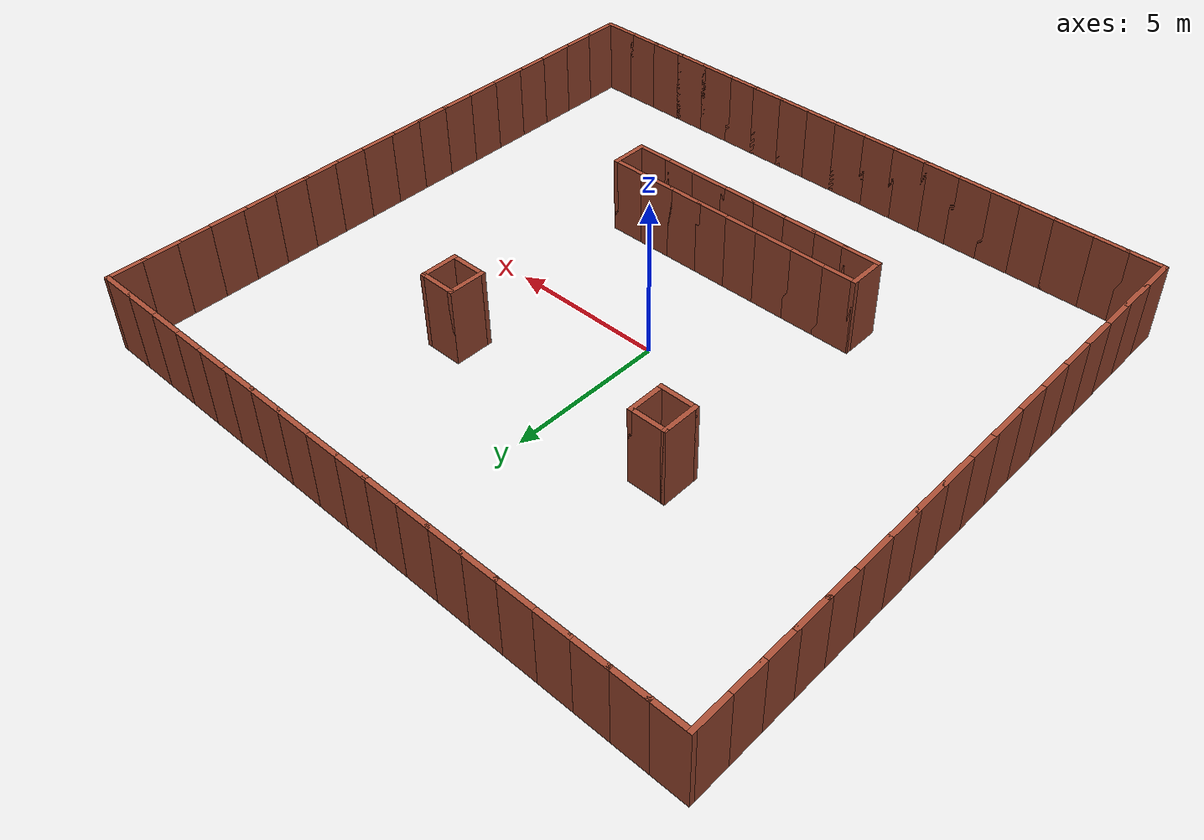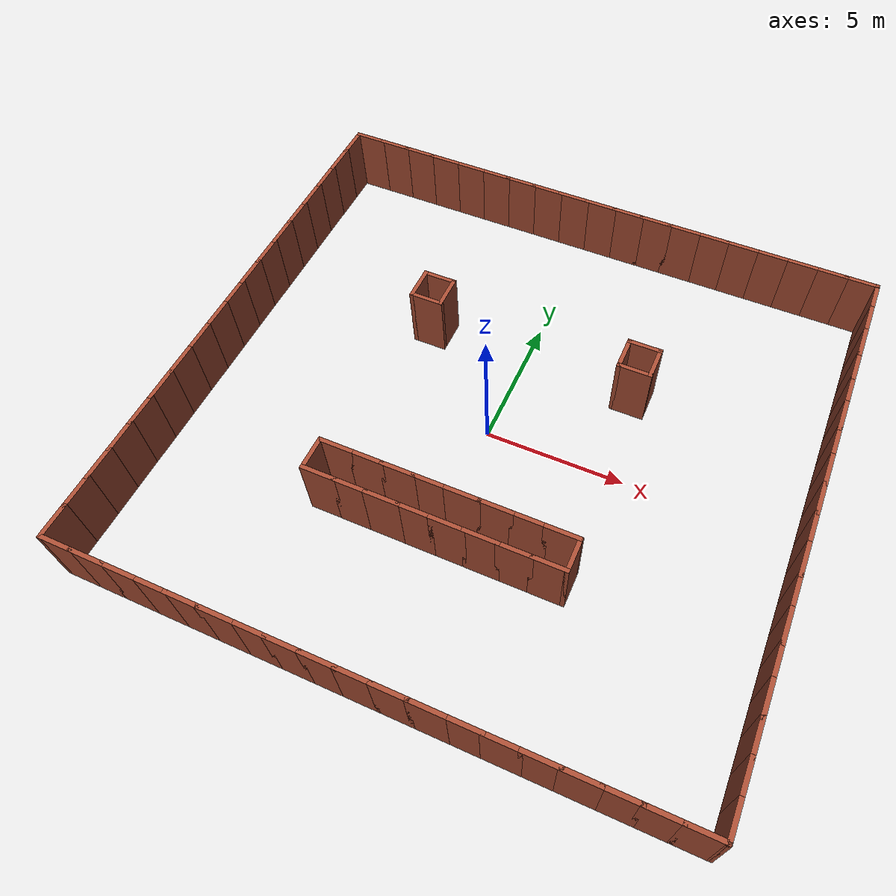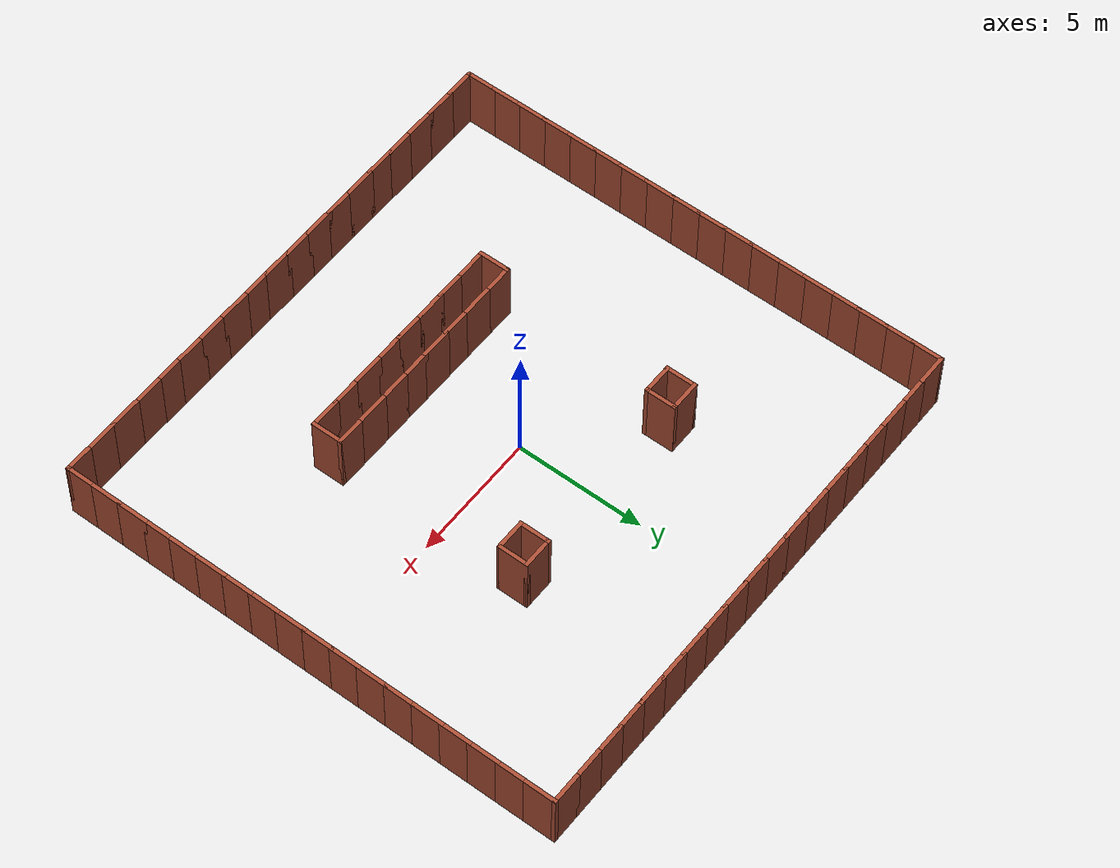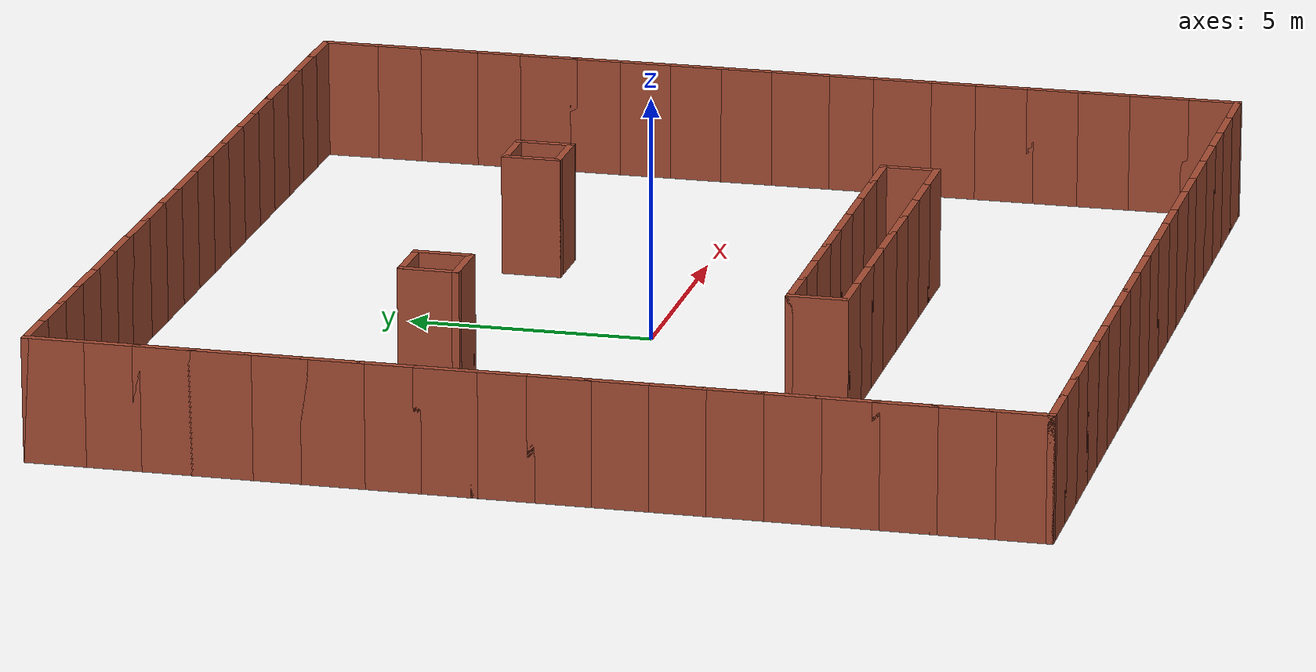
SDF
<?xml version='1.0'?>
<sdf version='1.7'>
  <model name='mapateste'>
    <pose>0.45 -0.1 0 0 -0 0</pose>
    <link name='Wall_100'>
      <collision name='Wall_100_Collision'>
        <geometry>
          <box>
            <size>1.25 0.15 2.5</size>
          </box>
        </geometry>
        <pose>0 0 1.25 0 -0 0</pose>
      </collision>
      <visual name='Wall_100_Visual'>
        <pose>0 0 1.25 0 -0 0</pose>
        <geometry>
          <box>
            <size>1.25 0.15 2.5</size>
          </box>
        </geometry>
        <material>
          <script>
            <uri>file://media/materials/scripts/gazebo.material</uri>
            <name>Gazebo/Bricks</name>
          </script>
          <ambient>1 1 1 1</ambient>
        </material>
        <meta>
          <layer>0</layer>
        </meta>
      </visual>
      <pose>9.9 9.9 0 0 -0 3.14159</pose>
    </link>
    <link name='Wall_101'>
      <collision name='Wall_101_Collision'>
        <geometry>
          <box>
            <size>1.25 0.15 2.5</size>
          </box>
        </geometry>
        <pose>0 0 1.25 0 -0 0</pose>
      </collision>
      <visual name='Wall_101_Visual'>
        <pose>0 0 1.25 0 -0 0</pose>
        <geometry>
          <box>
            <size>1.25 0.15 2.5</size>
          </box>
        </geometry>
        <material>
          <script>
            <uri>file://media/materials/scripts/gazebo.material</uri>
            <name>Gazebo/Bricks</name>
          </script>
          <ambient>1 1 1 1</ambient>
        </material>
        <meta>
          <layer>0</layer>
        </meta>
      </visual>
      <pose>8.8 9.9 0 0 -0 3.14159</pose>
    </link>
    <link name='Wall_102'>
      <collision name='Wall_102_Collision'>
        <geometry>
          <box>
            <size>1.25 0.15 2.5</size>
          </box>
        </geometry>
        <pose>0 0 1.25 0 -0 0</pose>
      </collision>
      <visual name='Wall_102_Visual'>
        <pose>0 0 1.25 0 -0 0</pose>
        <geometry>
          <box>
            <size>1.25 0.15 2.5</size>
          </box>
        </geometry>
        <material>
          <script>
            <uri>file://media/materials/scripts/gazebo.material</uri>
            <name>Gazebo/Bricks</name>
          </script>
          <ambient>1 1 1 1</ambient>
        </material>
        <meta>
          <layer>0</layer>
        </meta>
      </visual>
      <pose>7.7 9.9 0 0 -0 3.14159</pose>
    </link>
    <link name='Wall_103'>
      <collision name='Wall_103_Collision'>
        <geometry>
          <box>
            <size>1.25 0.15 2.5</size>
          </box>
        </geometry>
        <pose>0 0 1.25 0 -0 0</pose>
      </collision>
      <visual name='Wall_103_Visual'>
        <pose>0 0 1.25 0 -0 0</pose>
        <geometry>
          <box>
            <size>1.25 0.15 2.5</size>
          </box>
        </geometry>
        <material>
          <script>
            <uri>file://media/materials/scripts/gazebo.material</uri>
            <name>Gazebo/Bricks</name>
          </script>
          <ambient>1 1 1 1</ambient>
        </material>
        <meta>
          <layer>0</layer>
        </meta>
      </visual>
      <pose>6.6 9.9 0 0 -0 3.14159</pose>
    </link>
    <link name='Wall_104'>
      <collision name='Wall_104_Collision'>
        <geometry>
          <box>
            <size>1.25 0.15 2.5</size>
          </box>
        </geometry>
        <pose>0 0 1.25 0 -0 0</pose>
      </collision>
      <visual name='Wall_104_Visual'>
        <pose>0 0 1.25 0 -0 0</pose>
        <geometry>
          <box>
            <size>1.25 0.15 2.5</size>
          </box>
        </geometry>
        <material>
          <script>
            <uri>file://media/materials/scripts/gazebo.material</uri>
            <name>Gazebo/Bricks</name>
          </script>
          <ambient>1 1 1 1</ambient>
        </material>
        <meta>
          <layer>0</layer>
        </meta>
      </visual>
      <pose>5.5 9.9 0 0 -0 3.14159</pose>
    </link>
    <link name='Wall_105'>
      <collision name='Wall_105_Collision'>
        <geometry>
          <box>
            <size>1.25 0.15 2.5</size>
          </box>
        </geometry>
        <pose>0 0 1.25 0 -0 0</pose>
      </collision>
      <visual name='Wall_105_Visual'>
        <pose>0 0 1.25 0 -0 0</pose>
        <geometry>
          <box>
            <size>1.25 0.15 2.5</size>
          </box>
        </geometry>
        <material>
          <script>
            <uri>file://media/materials/scripts/gazebo.material</uri>
            <name>Gazebo/Bricks</name>
          </script>
          <ambient>1 1 1 1</ambient>
        </material>
        <meta>
          <layer>0</layer>
        </meta>
      </visual>
      <pose>4.4 9.9 0 0 -0 3.14159</pose>
    </link>
    <link name='Wall_106'>
      <collision name='Wall_106_Collision'>
        <geometry>
          <box>
            <size>1.25 0.15 2.5</size>
          </box>
        </geometry>
        <pose>0 0 1.25 0 -0 0</pose>
      </collision>
      <visual name='Wall_106_Visual'>
        <pose>0 0 1.25 0 -0 0</pose>
        <geometry>
          <box>
            <size>1.25 0.15 2.5</size>
          </box>
        </geometry>
        <material>
          <script>
            <uri>file://media/materials/scripts/gazebo.material</uri>
            <name>Gazebo/Bricks</name>
          </script>
          <ambient>1 1 1 1</ambient>
        </material>
        <meta>
          <layer>0</layer>
        </meta>
      </visual>
      <pose>3.3 9.9 0 0 -0 3.14159</pose>
    </link>
    <link name='Wall_107'>
      <collision name='Wall_107_Collision'>
        <geometry>
          <box>
            <size>1.25 0.15 2.5</size>
          </box>
        </geometry>
        <pose>0 0 1.25 0 -0 0</pose>
      </collision>
      <visual name='Wall_107_Visual'>
        <pose>0 0 1.25 0 -0 0</pose>
        <geometry>
          <box>
            <size>1.25 0.15 2.5</size>
          </box>
        </geometry>
        <material>
          <script>
            <uri>file://media/materials/scripts/gazebo.material</uri>
            <name>Gazebo/Bricks</name>
          </script>
          <ambient>1 1 1 1</ambient>
        </material>
        <meta>
          <layer>0</layer>
        </meta>
      </visual>
      <pose>2.2 9.9 0 0 -0 3.14159</pose>
    </link>
    <link name='Wall_109'>
      <collision name='Wall_109_Collision'>
        <geometry>
          <box>
            <size>1.25 0.15 2.5</size>
          </box>
        </geometry>
        <pose>0 0 1.25 0 -0 0</pose>
      </collision>
      <visual name='Wall_109_Visual'>
        <pose>0 0 1.25 0 -0 0</pose>
        <geometry>
          <box>
            <size>1.25 0.15 2.5</size>
          </box>
        </geometry>
        <material>
          <script>
            <uri>file://media/materials/scripts/gazebo.material</uri>
            <name>Gazebo/Bricks</name>
          </script>
          <ambient>1 1 1 1</ambient>
        </material>
        <meta>
          <layer>0</layer>
        </meta>
      </visual>
      <pose>1.1 9.9 0 0 -0 3.14159</pose>
    </link>
    <link name='Wall_110'>
      <collision name='Wall_110_Collision'>
        <geometry>
          <box>
            <size>1.25 0.15 2.5</size>
          </box>
        </geometry>
        <pose>0 0 1.25 0 -0 0</pose>
      </collision>
      <visual name='Wall_110_Visual'>
        <pose>0 0 1.25 0 -0 0</pose>
        <geometry>
          <box>
            <size>1.25 0.15 2.5</size>
          </box>
        </geometry>
        <material>
          <script>
            <uri>file://media/materials/scripts/gazebo.material</uri>
            <name>Gazebo/Bricks</name>
          </script>
          <ambient>1 1 1 1</ambient>
        </material>
        <meta>
          <layer>0</layer>
        </meta>
      </visual>
      <pose>-0 9.9 0 0 -0 3.14159</pose>
    </link>
    <link name='Wall_111'>
      <collision name='Wall_111_Collision'>
        <geometry>
          <box>
            <size>1.25 0.15 2.5</size>
          </box>
        </geometry>
        <pose>0 0 1.25 0 -0 0</pose>
      </collision>
      <visual name='Wall_111_Visual'>
        <pose>0 0 1.25 0 -0 0</pose>
        <geometry>
          <box>
            <size>1.25 0.15 2.5</size>
          </box>
        </geometry>
        <material>
          <script>
            <uri>file://media/materials/scripts/gazebo.material</uri>
            <name>Gazebo/Bricks</name>
          </script>
          <ambient>1 1 1 1</ambient>
        </material>
        <meta>
          <layer>0</layer>
        </meta>
      </visual>
      <pose>-1.1 9.9 0 0 -0 3.14159</pose>
    </link>
    <link name='Wall_112'>
      <collision name='Wall_112_Collision'>
        <geometry>
          <box>
            <size>1.25 0.15 2.5</size>
          </box>
        </geometry>
        <pose>0 0 1.25 0 -0 0</pose>
      </collision>
      <visual name='Wall_112_Visual'>
        <pose>0 0 1.25 0 -0 0</pose>
        <geometry>
          <box>
            <size>1.25 0.15 2.5</size>
          </box>
        </geometry>
        <material>
          <script>
            <uri>file://media/materials/scripts/gazebo.material</uri>
            <name>Gazebo/Bricks</name>
          </script>
          <ambient>1 1 1 1</ambient>
        </material>
        <meta>
          <layer>0</layer>
        </meta>
      </visual>
      <pose>-2.2 9.9 0 0 -0 3.14159</pose>
    </link>
    <link name='Wall_113'>
      <collision name='Wall_113_Collision'>
        <geometry>
          <box>
            <size>1.25 0.15 2.5</size>
          </box>
        </geometry>
        <pose>0 0 1.25 0 -0 0</pose>
      </collision>
      <visual name='Wall_113_Visual'>
        <pose>0 0 1.25 0 -0 0</pose>
        <geometry>
          <box>
            <size>1.25 0.15 2.5</size>
          </box>
        </geometry>
        <material>
          <script>
            <uri>file://media/materials/scripts/gazebo.material</uri>
            <name>Gazebo/Bricks</name>
          </script>
          <ambient>1 1 1 1</ambient>
        </material>
        <meta>
          <layer>0</layer>
        </meta>
      </visual>
      <pose>-3.3 9.9 0 0 -0 3.14159</pose>
    </link>
    <link name='Wall_114'>
      <collision name='Wall_114_Collision'>
        <geometry>
          <box>
            <size>1.25 0.15 2.5</size>
          </box>
        </geometry>
        <pose>0 0 1.25 0 -0 0</pose>
      </collision>
      <visual name='Wall_114_Visual'>
        <pose>0 0 1.25 0 -0 0</pose>
        <geometry>
          <box>
            <size>1.25 0.15 2.5</size>
          </box>
        </geometry>
        <material>
          <script>
            <uri>file://media/materials/scripts/gazebo.material</uri>
            <name>Gazebo/Bricks</name>
          </script>
          <ambient>1 1 1 1</ambient>
        </material>
        <meta>
          <layer>0</layer>
        </meta>
      </visual>
      <pose>-4.4 9.9 0 0 -0 3.14159</pose>
    </link>
    <link name='Wall_115'>
      <collision name='Wall_115_Collision'>
        <geometry>
          <box>
            <size>1.25 0.15 2.5</size>
          </box>
        </geometry>
        <pose>0 0 1.25 0 -0 0</pose>
      </collision>
      <visual name='Wall_115_Visual'>
        <pose>0 0 1.25 0 -0 0</pose>
        <geometry>
          <box>
            <size>1.25 0.15 2.5</size>
          </box>
        </geometry>
        <material>
          <script>
            <uri>file://media/materials/scripts/gazebo.material</uri>
            <name>Gazebo/Bricks</name>
          </script>
          <ambient>1 1 1 1</ambient>
        </material>
        <meta>
          <layer>0</layer>
        </meta>
      </visual>
      <pose>-5.5 9.9 0 0 -0 3.14159</pose>
    </link>
    <link name='Wall_116'>
      <collision name='Wall_116_Collision'>
        <geometry>
          <box>
            <size>1.25 0.15 2.5</size>
          </box>
        </geometry>
        <pose>0 0 1.25 0 -0 0</pose>
      </collision>
      <visual name='Wall_116_Visual'>
        <pose>0 0 1.25 0 -0 0</pose>
        <geometry>
          <box>
            <size>1.25 0.15 2.5</size>
          </box>
        </geometry>
        <material>
          <script>
            <uri>file://media/materials/scripts/gazebo.material</uri>
            <name>Gazebo/Bricks</name>
          </script>
          <ambient>1 1 1 1</ambient>
        </material>
        <meta>
          <layer>0</layer>
        </meta>
      </visual>
      <pose>-6.6 9.9 0 0 -0 3.14159</pose>
    </link>
    <link name='Wall_117'>
      <collision name='Wall_117_Collision'>
        <geometry>
          <box>
            <size>1.25 0.15 2.5</size>
          </box>
        </geometry>
        <pose>0 0 1.25 0 -0 0</pose>
      </collision>
      <visual name='Wall_117_Visual'>
        <pose>0 0 1.25 0 -0 0</pose>
        <geometry>
          <box>
            <size>1.25 0.15 2.5</size>
          </box>
        </geometry>
        <material>
          <script>
            <uri>file://media/materials/scripts/gazebo.material</uri>
            <name>Gazebo/Bricks</name>
          </script>
          <ambient>1 1 1 1</ambient>
        </material>
        <meta>
          <layer>0</layer>
        </meta>
      </visual>
      <pose>-7.7 9.9 0 0 -0 3.14159</pose>
    </link>
    <link name='Wall_118'>
      <collision name='Wall_118_Collision'>
        <geometry>
          <box>
            <size>1.25 0.15 2.5</size>
          </box>
        </geometry>
        <pose>0 0 1.25 0 -0 0</pose>
      </collision>
      <visual name='Wall_118_Visual'>
        <pose>0 0 1.25 0 -0 0</pose>
        <geometry>
          <box>
            <size>1.25 0.15 2.5</size>
          </box>
        </geometry>
        <material>
          <script>
            <uri>file://media/materials/scripts/gazebo.material</uri>
            <name>Gazebo/Bricks</name>
          </script>
          <ambient>1 1 1 1</ambient>
        </material>
        <meta>
          <layer>0</layer>
        </meta>
      </visual>
      <pose>-8.8 9.9 0 0 -0 3.14159</pose>
    </link>
    <link name='Wall_119'>
      <collision name='Wall_119_Collision'>
        <geometry>
          <box>
            <size>1.25 0.15 2.5</size>
          </box>
        </geometry>
        <pose>0 0 1.25 0 -0 0</pose>
      </collision>
      <visual name='Wall_119_Visual'>
        <pose>0 0 1.25 0 -0 0</pose>
        <geometry>
          <box>
            <size>1.25 0.15 2.5</size>
          </box>
        </geometry>
        <material>
          <script>
            <uri>file://media/materials/scripts/gazebo.material</uri>
            <name>Gazebo/Bricks</name>
          </script>
          <ambient>1 1 1 1</ambient>
        </material>
        <meta>
          <layer>0</layer>
        </meta>
      </visual>
      <pose>-9.9 9.9 0 0 -0 3.14159</pose>
    </link>
    <link name='Wall_120'>
      <collision name='Wall_120_Collision'>
        <geometry>
          <box>
            <size>1.25 0.15 2.5</size>
          </box>
        </geometry>
        <pose>0 0 1.25 0 -0 0</pose>
      </collision>
      <visual name='Wall_120_Visual'>
        <pose>0 0 1.25 0 -0 0</pose>
        <geometry>
          <box>
            <size>1.25 0.15 2.5</size>
          </box>
        </geometry>
        <material>
          <script>
            <uri>file://media/materials/scripts/gazebo.material</uri>
            <name>Gazebo/Bricks</name>
          </script>
          <ambient>1 1 1 1</ambient>
        </material>
        <meta>
          <layer>0</layer>
        </meta>
      </visual>
      <pose>-10.45 9.35 0 0 -0 -1.5708</pose>
    </link>
    <link name='Wall_126'>
      <collision name='Wall_126_Collision'>
        <geometry>
          <box>
            <size>1.25 0.15 2.5</size>
          </box>
        </geometry>
        <pose>0 0 1.25 0 -0 0</pose>
      </collision>
      <visual name='Wall_126_Visual'>
        <pose>0 0 1.25 0 -0 0</pose>
        <geometry>
          <box>
            <size>1.25 0.15 2.5</size>
          </box>
        </geometry>
        <material>
          <script>
            <uri>file://media/materials/scripts/gazebo.material</uri>
            <name>Gazebo/Bricks</name>
          </script>
          <ambient>1 1 1 1</ambient>
        </material>
        <meta>
          <layer>0</layer>
        </meta>
      </visual>
      <pose>-10.45 3.85 0 0 -0 -1.5708</pose>
    </link>
    <link name='Wall_127'>
      <collision name='Wall_127_Collision'>
        <geometry>
          <box>
            <size>1.25 0.15 2.5</size>
          </box>
        </geometry>
        <pose>0 0 1.25 0 -0 0</pose>
      </collision>
      <visual name='Wall_127_Visual'>
        <pose>0 0 1.25 0 -0 0</pose>
        <geometry>
          <box>
            <size>1.25 0.15 2.5</size>
          </box>
        </geometry>
        <material>
          <script>
            <uri>file://media/materials/scripts/gazebo.material</uri>
            <name>Gazebo/Bricks</name>
          </script>
          <ambient>1 1 1 1</ambient>
        </material>
        <meta>
          <layer>0</layer>
        </meta>
      </visual>
      <pose>-10.45 2.75 0 0 -0 -1.5708</pose>
    </link>
    <link name='Wall_128'>
      <collision name='Wall_128_Collision'>
        <geometry>
          <box>
            <size>1.25 0.15 2.5</size>
          </box>
        </geometry>
        <pose>0 0 1.25 0 -0 0</pose>
      </collision>
      <visual name='Wall_128_Visual'>
        <pose>0 0 1.25 0 -0 0</pose>
        <geometry>
          <box>
            <size>1.25 0.15 2.5</size>
          </box>
        </geometry>
        <material>
          <script>
            <uri>file://media/materials/scripts/gazebo.material</uri>
            <name>Gazebo/Bricks</name>
          </script>
          <ambient>1 1 1 1</ambient>
        </material>
        <meta>
          <layer>0</layer>
        </meta>
      </visual>
      <pose>-10.45 1.65 0 0 -0 -1.5708</pose>
    </link>
    <link name='Wall_129'>
      <collision name='Wall_129_Collision'>
        <geometry>
          <box>
            <size>1.25 0.15 2.5</size>
          </box>
        </geometry>
        <pose>0 0 1.25 0 -0 0</pose>
      </collision>
      <visual name='Wall_129_Visual'>
        <pose>0 0 1.25 0 -0 0</pose>
        <geometry>
          <box>
            <size>1.25 0.15 2.5</size>
          </box>
        </geometry>
        <material>
          <script>
            <uri>file://media/materials/scripts/gazebo.material</uri>
            <name>Gazebo/Bricks</name>
          </script>
          <ambient>1 1 1 1</ambient>
        </material>
        <meta>
          <layer>0</layer>
        </meta>
      </visual>
      <pose>-10.45 0.55 0 0 -0 -1.5708</pose>
    </link>
    <link name='Wall_130'>
      <collision name='Wall_130_Collision'>
        <geometry>
          <box>
            <size>1.25 0.15 2.5</size>
          </box>
        </geometry>
        <pose>0 0 1.25 0 -0 0</pose>
      </collision>
      <visual name='Wall_130_Visual'>
        <pose>0 0 1.25 0 -0 0</pose>
        <geometry>
          <box>
            <size>1.25 0.15 2.5</size>
          </box>
        </geometry>
        <material>
          <script>
            <uri>file://media/materials/scripts/gazebo.material</uri>
            <name>Gazebo/Bricks</name>
          </script>
          <ambient>1 1 1 1</ambient>
        </material>
        <meta>
          <layer>0</layer>
        </meta>
      </visual>
      <pose>-10.45 -0.55 0 0 -0 -1.5708</pose>
    </link>
    <link name='Wall_131'>
      <collision name='Wall_131_Collision'>
        <geometry>
          <box>
            <size>1.25 0.15 2.5</size>
          </box>
        </geometry>
        <pose>0 0 1.25 0 -0 0</pose>
      </collision>
      <visual name='Wall_131_Visual'>
        <pose>0 0 1.25 0 -0 0</pose>
        <geometry>
          <box>
            <size>1.25 0.15 2.5</size>
          </box>
        </geometry>
        <material>
          <script>
            <uri>file://media/materials/scripts/gazebo.material</uri>
            <name>Gazebo/Bricks</name>
          </script>
          <ambient>1 1 1 1</ambient>
        </material>
        <meta>
          <layer>0</layer>
        </meta>
      </visual>
      <pose>-10.45 -1.65 0 0 -0 -1.5708</pose>
    </link>
    <link name='Wall_132'>
      <collision name='Wall_132_Collision'>
        <geometry>
          <box>
            <size>1.25 0.15 2.5</size>
          </box>
        </geometry>
        <pose>0 0 1.25 0 -0 0</pose>
      </collision>
      <visual name='Wall_132_Visual'>
        <pose>0 0 1.25 0 -0 0</pose>
        <geometry>
          <box>
            <size>1.25 0.15 2.5</size>
          </box>
        </geometry>
        <material>
          <script>
            <uri>file://media/materials/scripts/gazebo.material</uri>
            <name>Gazebo/Bricks</name>
          </script>
          <ambient>1 1 1 1</ambient>
        </material>
        <meta>
          <layer>0</layer>
        </meta>
      </visual>
      <pose>-10.45 -2.75 0 0 -0 -1.5708</pose>
    </link>
    <link name='Wall_133'>
      <collision name='Wall_133_Collision'>
        <geometry>
          <box>
            <size>1.25 0.15 2.5</size>
          </box>
        </geometry>
        <pose>0 0 1.25 0 -0 0</pose>
      </collision>
      <visual name='Wall_133_Visual'>
        <pose>0 0 1.25 0 -0 0</pose>
        <geometry>
          <box>
            <size>1.25 0.15 2.5</size>
          </box>
        </geometry>
        <material>
          <script>
            <uri>file://media/materials/scripts/gazebo.material</uri>
            <name>Gazebo/Bricks</name>
          </script>
          <ambient>1 1 1 1</ambient>
        </material>
        <meta>
          <layer>0</layer>
        </meta>
      </visual>
      <pose>-10.45 -3.85 0 0 -0 -1.5708</pose>
    </link>
    <link name='Wall_134'>
      <collision name='Wall_134_Collision'>
        <geometry>
          <box>
            <size>1.25 0.15 2.5</size>
          </box>
        </geometry>
        <pose>0 0 1.25 0 -0 0</pose>
      </collision>
      <visual name='Wall_134_Visual'>
        <pose>0 0 1.25 0 -0 0</pose>
        <geometry>
          <box>
            <size>1.25 0.15 2.5</size>
          </box>
        </geometry>
        <material>
          <script>
            <uri>file://media/materials/scripts/gazebo.material</uri>
            <name>Gazebo/Bricks</name>
          </script>
          <ambient>1 1 1 1</ambient>
        </material>
        <meta>
          <layer>0</layer>
        </meta>
      </visual>
      <pose>-10.45 -4.95 0 0 -0 -1.5708</pose>
    </link>
    <link name='Wall_135'>
      <collision name='Wall_135_Collision'>
        <geometry>
          <box>
            <size>1.25 0.15 2.5</size>
          </box>
        </geometry>
        <pose>0 0 1.25 0 -0 0</pose>
      </collision>
      <visual name='Wall_135_Visual'>
        <pose>0 0 1.25 0 -0 0</pose>
        <geometry>
          <box>
            <size>1.25 0.15 2.5</size>
          </box>
        </geometry>
        <material>
          <script>
            <uri>file://media/materials/scripts/gazebo.material</uri>
            <name>Gazebo/Bricks</name>
          </script>
          <ambient>1 1 1 1</ambient>
        </material>
        <meta>
          <layer>0</layer>
        </meta>
      </visual>
      <pose>-10.45 -6.05 0 0 -0 -1.5708</pose>
    </link>
    <link name='Wall_136'>
      <collision name='Wall_136_Collision'>
        <geometry>
          <box>
            <size>1.25 0.15 2.5</size>
          </box>
        </geometry>
        <pose>0 0 1.25 0 -0 0</pose>
      </collision>
      <visual name='Wall_136_Visual'>
        <pose>0 0 1.25 0 -0 0</pose>
        <geometry>
          <box>
            <size>1.25 0.15 2.5</size>
          </box>
        </geometry>
        <material>
          <script>
            <uri>file://media/materials/scripts/gazebo.material</uri>
            <name>Gazebo/Bricks</name>
          </script>
          <ambient>1 1 1 1</ambient>
        </material>
        <meta>
          <layer>0</layer>
        </meta>
      </visual>
      <pose>-10.45 -7.15 0 0 -0 -1.5708</pose>
    </link>
    <link name='Wall_137'>
      <collision name='Wall_137_Collision'>
        <geometry>
          <box>
            <size>1.25 0.15 2.5</size>
          </box>
        </geometry>
        <pose>0 0 1.25 0 -0 0</pose>
      </collision>
      <visual name='Wall_137_Visual'>
        <pose>0 0 1.25 0 -0 0</pose>
        <geometry>
          <box>
            <size>1.25 0.15 2.5</size>
          </box>
        </geometry>
        <material>
          <script>
            <uri>file://media/materials/scripts/gazebo.material</uri>
            <name>Gazebo/Bricks</name>
          </script>
          <ambient>1 1 1 1</ambient>
        </material>
        <meta>
          <layer>0</layer>
        </meta>
      </visual>
      <pose>-10.45 -8.25 0 0 -0 -1.5708</pose>
    </link>
    <link name='Wall_138'>
      <collision name='Wall_138_Collision'>
        <geometry>
          <box>
            <size>1.25 0.15 2.5</size>
          </box>
        </geometry>
        <pose>0 0 1.25 0 -0 0</pose>
      </collision>
      <visual name='Wall_138_Visual'>
        <pose>0 0 1.25 0 -0 0</pose>
        <geometry>
          <box>
            <size>1.25 0.15 2.5</size>
          </box>
        </geometry>
        <material>
          <script>
            <uri>file://media/materials/scripts/gazebo.material</uri>
            <name>Gazebo/Bricks</name>
          </script>
          <ambient>1 1 1 1</ambient>
        </material>
        <meta>
          <layer>0</layer>
        </meta>
      </visual>
      <pose>-10.45 -9.35 0 0 -0 -1.5708</pose>
    </link>
    <link name='Wall_142'>
      <collision name='Wall_142_Collision'>
        <geometry>
          <box>
            <size>1.25 0.15 2.5</size>
          </box>
        </geometry>
        <pose>0 0 1.25 0 -0 0</pose>
      </collision>
      <visual name='Wall_142_Visual'>
        <pose>0 0 1.25 0 -0 0</pose>
        <geometry>
          <box>
            <size>1.25 0.15 2.5</size>
          </box>
        </geometry>
        <material>
          <script>
            <uri>file://media/materials/scripts/gazebo.material</uri>
            <name>Gazebo/Bricks</name>
          </script>
          <ambient>1 1 1 1</ambient>
        </material>
        <meta>
          <layer>0</layer>
        </meta>
      </visual>
      <pose>-4.60633 3.55566 0 0 -0 1.5708</pose>
    </link>
    <link name='Wall_144'>
      <collision name='Wall_144_Collision'>
        <geometry>
          <box>
            <size>1.25 0.15 2.5</size>
          </box>
        </geometry>
        <pose>0 0 1.25 0 -0 0</pose>
      </collision>
      <visual name='Wall_144_Visual'>
        <pose>0 0 1.25 0 -0 0</pose>
        <geometry>
          <box>
            <size>1.25 0.15 2.5</size>
          </box>
        </geometry>
        <material>
          <script>
            <uri>file://media/materials/scripts/gazebo.material</uri>
            <name>Gazebo/Bricks</name>
          </script>
          <ambient>1 1 1 1</ambient>
        </material>
        <meta>
          <layer>0</layer>
        </meta>
      </visual>
      <pose>-10.45 8.25 0 0 -0 -1.5708</pose>
    </link>
    <link name='Wall_145'>
      <collision name='Wall_145_Collision'>
        <geometry>
          <box>
            <size>1.25 0.15 2.5</size>
          </box>
        </geometry>
        <pose>0 0 1.25 0 -0 0</pose>
      </collision>
      <visual name='Wall_145_Visual'>
        <pose>0 0 1.25 0 -0 0</pose>
        <geometry>
          <box>
            <size>1.25 0.15 2.5</size>
          </box>
        </geometry>
        <material>
          <script>
            <uri>file://media/materials/scripts/gazebo.material</uri>
            <name>Gazebo/Bricks</name>
          </script>
          <ambient>1 1 1 1</ambient>
        </material>
        <meta>
          <layer>0</layer>
        </meta>
      </visual>
      <pose>-10.45 7.15 0 0 -0 -1.5708</pose>
    </link>
    <link name='Wall_146'>
      <collision name='Wall_146_Collision'>
        <geometry>
          <box>
            <size>1.25 0.15 2.5</size>
          </box>
        </geometry>
        <pose>0 0 1.25 0 -0 0</pose>
      </collision>
      <visual name='Wall_146_Visual'>
        <pose>0 0 1.25 0 -0 0</pose>
        <geometry>
          <box>
            <size>1.25 0.15 2.5</size>
          </box>
        </geometry>
        <material>
          <script>
            <uri>file://media/materials/scripts/gazebo.material</uri>
            <name>Gazebo/Bricks</name>
          </script>
          <ambient>1 1 1 1</ambient>
        </material>
        <meta>
          <layer>0</layer>
        </meta>
      </visual>
      <pose>-10.45 6.05 0 0 -0 -1.5708</pose>
    </link>
    <link name='Wall_147'>
      <collision name='Wall_147_Collision'>
        <geometry>
          <box>
            <size>1.25 0.15 2.5</size>
          </box>
        </geometry>
        <pose>0 0 1.25 0 -0 0</pose>
      </collision>
      <visual name='Wall_147_Visual'>
        <pose>0 0 1.25 0 -0 0</pose>
        <geometry>
          <box>
            <size>1.25 0.15 2.5</size>
          </box>
        </geometry>
        <material>
          <script>
            <uri>file://media/materials/scripts/gazebo.material</uri>
            <name>Gazebo/Bricks</name>
          </script>
          <ambient>1 1 1 1</ambient>
        </material>
        <meta>
          <layer>0</layer>
        </meta>
      </visual>
      <pose>-10.45 4.95 0 0 -0 -1.5708</pose>
    </link>
    <link name='Wall_155'>
      <collision name='Wall_155_Collision'>
        <geometry>
          <box>
            <size>1.25 0.15 2.5</size>
          </box>
        </geometry>
        <pose>0 0 1.25 0 -0 0</pose>
      </collision>
      <visual name='Wall_155_Visual'>
        <pose>0 0 1.25 0 -0 0</pose>
        <geometry>
          <box>
            <size>1.25 0.15 2.5</size>
          </box>
        </geometry>
        <material>
          <script>
            <uri>file://media/materials/scripts/gazebo.material</uri>
            <name>Gazebo/Bricks</name>
          </script>
          <ambient>1 1 1 1</ambient>
        </material>
        <meta>
          <layer>0</layer>
        </meta>
      </visual>
      <pose>-4.05633 4.10566 0 0 -0 0</pose>
    </link>
    <link name='Wall_156'>
      <collision name='Wall_156_Collision'>
        <geometry>
          <box>
            <size>1.25 0.15 2.5</size>
          </box>
        </geometry>
        <pose>0 0 1.25 0 -0 0</pose>
      </collision>
      <visual name='Wall_156_Visual'>
        <pose>0 0 1.25 0 -0 0</pose>
        <geometry>
          <box>
            <size>1.25 0.15 2.5</size>
          </box>
        </geometry>
        <material>
          <script>
            <uri>file://media/materials/scripts/gazebo.material</uri>
            <name>Gazebo/Bricks</name>
          </script>
          <ambient>1 1 1 1</ambient>
        </material>
        <meta>
          <layer>0</layer>
        </meta>
      </visual>
      <pose>-3.50633 3.55566 0 0 -0 -1.5708</pose>
    </link>
    <link name='Wall_157'>
      <collision name='Wall_157_Collision'>
        <geometry>
          <box>
            <size>1.25 0.15 2.5</size>
          </box>
        </geometry>
        <pose>0 0 1.25 0 -0 0</pose>
      </collision>
      <visual name='Wall_157_Visual'>
        <pose>0 0 1.25 0 -0 0</pose>
        <geometry>
          <box>
            <size>1.25 0.15 2.5</size>
          </box>
        </geometry>
        <material>
          <script>
            <uri>file://media/materials/scripts/gazebo.material</uri>
            <name>Gazebo/Bricks</name>
          </script>
          <ambient>1 1 1 1</ambient>
        </material>
        <meta>
          <layer>0</layer>
        </meta>
      </visual>
      <pose>-4.05633 3.00566 0 0 -0 3.14159</pose>
    </link>
    <link name='Wall_159'>
      <collision name='Wall_159_Collision'>
        <geometry>
          <box>
            <size>1.25 0.15 2.5</size>
          </box>
        </geometry>
        <pose>0 0 1.25 0 -0 0</pose>
      </collision>
      <visual name='Wall_159_Visual'>
        <pose>0 0 1.25 0 -0 0</pose>
        <geometry>
          <box>
            <size>1.25 0.15 2.5</size>
          </box>
        </geometry>
        <material>
          <script>
            <uri>file://media/materials/scripts/gazebo.material</uri>
            <name>Gazebo/Bricks</name>
          </script>
          <ambient>1 1 1 1</ambient>
        </material>
        <meta>
          <layer>0</layer>
        </meta>
      </visual>
      <pose>4.24775 3.46923 0 0 -0 -1.5708</pose>
    </link>
    <link name='Wall_169'>
      <collision name='Wall_169_Collision'>
        <geometry>
          <box>
            <size>1.25 0.15 2.5</size>
          </box>
        </geometry>
        <pose>0 0 1.25 0 -0 0</pose>
      </collision>
      <visual name='Wall_169_Visual'>
        <pose>0 0 1.25 0 -0 0</pose>
        <geometry>
          <box>
            <size>1.25 0.15 2.5</size>
          </box>
        </geometry>
        <material>
          <script>
            <uri>file://media/materials/scripts/gazebo.material</uri>
            <name>Gazebo/Bricks</name>
          </script>
          <ambient>1 1 1 1</ambient>
        </material>
        <meta>
          <layer>0</layer>
        </meta>
      </visual>
      <pose>-4.55922 -4.19159 0 0 -0 -1.5708</pose>
    </link>
    <link name='Wall_174'>
      <collision name='Wall_174_Collision'>
        <geometry>
          <box>
            <size>1.25 0.15 2.5</size>
          </box>
        </geometry>
        <pose>0 0 1.25 0 -0 0</pose>
      </collision>
      <visual name='Wall_174_Visual'>
        <pose>0 0 1.25 0 -0 0</pose>
        <geometry>
          <box>
            <size>1.25 0.15 2.5</size>
          </box>
        </geometry>
        <material>
          <script>
            <uri>file://media/materials/scripts/gazebo.material</uri>
            <name>Gazebo/Bricks</name>
          </script>
          <ambient>1 1 1 1</ambient>
        </material>
        <meta>
          <layer>0</layer>
        </meta>
      </visual>
      <pose>-4.00922 -4.74159 0 0 -0 0</pose>
    </link>
    <link name='Wall_175'>
      <collision name='Wall_175_Collision'>
        <geometry>
          <box>
            <size>1.25 0.15 2.5</size>
          </box>
        </geometry>
        <pose>0 0 1.25 0 -0 0</pose>
      </collision>
      <visual name='Wall_175_Visual'>
        <pose>0 0 1.25 0 -0 0</pose>
        <geometry>
          <box>
            <size>1.25 0.15 2.5</size>
          </box>
        </geometry>
        <material>
          <script>
            <uri>file://media/materials/scripts/gazebo.material</uri>
            <name>Gazebo/Bricks</name>
          </script>
          <ambient>1 1 1 1</ambient>
        </material>
        <meta>
          <layer>0</layer>
        </meta>
      </visual>
      <pose>-2.90922 -4.74159 0 0 -0 0</pose>
    </link>
    <link name='Wall_176'>
      <collision name='Wall_176_Collision'>
        <geometry>
          <box>
            <size>1.25 0.15 2.5</size>
          </box>
        </geometry>
        <pose>0 0 1.25 0 -0 0</pose>
      </collision>
      <visual name='Wall_176_Visual'>
        <pose>0 0 1.25 0 -0 0</pose>
        <geometry>
          <box>
            <size>1.25 0.15 2.5</size>
          </box>
        </geometry>
        <material>
          <script>
            <uri>file://media/materials/scripts/gazebo.material</uri>
            <name>Gazebo/Bricks</name>
          </script>
          <ambient>1 1 1 1</ambient>
        </material>
        <meta>
          <layer>0</layer>
        </meta>
      </visual>
      <pose>-1.80922 -4.74159 0 0 -0 0</pose>
    </link>
    <link name='Wall_177'>
      <collision name='Wall_177_Collision'>
        <geometry>
          <box>
            <size>1.25 0.15 2.5</size>
          </box>
        </geometry>
        <pose>0 0 1.25 0 -0 0</pose>
      </collision>
      <visual name='Wall_177_Visual'>
        <pose>0 0 1.25 0 -0 0</pose>
        <geometry>
          <box>
            <size>1.25 0.15 2.5</size>
          </box>
        </geometry>
        <material>
          <script>
            <uri>file://media/materials/scripts/gazebo.material</uri>
            <name>Gazebo/Bricks</name>
          </script>
          <ambient>1 1 1 1</ambient>
        </material>
        <meta>
          <layer>0</layer>
        </meta>
      </visual>
      <pose>-0.709218 -4.74159 0 0 -0 0</pose>
    </link>
    <link name='Wall_178'>
      <collision name='Wall_178_Collision'>
        <geometry>
          <box>
            <size>1.25 0.15 2.5</size>
          </box>
        </geometry>
        <pose>0 0 1.25 0 -0 0</pose>
      </collision>
      <visual name='Wall_178_Visual'>
        <pose>0 0 1.25 0 -0 0</pose>
        <geometry>
          <box>
            <size>1.25 0.15 2.5</size>
          </box>
        </geometry>
        <material>
          <script>
            <uri>file://media/materials/scripts/gazebo.material</uri>
            <name>Gazebo/Bricks</name>
          </script>
          <ambient>1 1 1 1</ambient>
        </material>
        <meta>
          <layer>0</layer>
        </meta>
      </visual>
      <pose>0.390782 -4.74159 0 0 -0 0</pose>
    </link>
    <link name='Wall_179'>
      <collision name='Wall_179_Collision'>
        <geometry>
          <box>
            <size>1.25 0.15 2.5</size>
          </box>
        </geometry>
        <pose>0 0 1.25 0 -0 0</pose>
      </collision>
      <visual name='Wall_179_Visual'>
        <pose>0 0 1.25 0 -0 0</pose>
        <geometry>
          <box>
            <size>1.25 0.15 2.5</size>
          </box>
        </geometry>
        <material>
          <script>
            <uri>file://media/materials/scripts/gazebo.material</uri>
            <name>Gazebo/Bricks</name>
          </script>
          <ambient>1 1 1 1</ambient>
        </material>
        <meta>
          <layer>0</layer>
        </meta>
      </visual>
      <pose>1.49078 -4.74159 0 0 -0 0</pose>
    </link>
    <link name='Wall_180'>
      <collision name='Wall_180_Collision'>
        <geometry>
          <box>
            <size>1.25 0.15 2.5</size>
          </box>
        </geometry>
        <pose>0 0 1.25 0 -0 0</pose>
      </collision>
      <visual name='Wall_180_Visual'>
        <pose>0 0 1.25 0 -0 0</pose>
        <geometry>
          <box>
            <size>1.25 0.15 2.5</size>
          </box>
        </geometry>
        <material>
          <script>
            <uri>file://media/materials/scripts/gazebo.material</uri>
            <name>Gazebo/Bricks</name>
          </script>
          <ambient>1 1 1 1</ambient>
        </material>
        <meta>
          <layer>0</layer>
        </meta>
      </visual>
      <pose>2.59078 -4.74159 0 0 -0 0</pose>
    </link>
    <link name='Wall_181'>
      <collision name='Wall_181_Collision'>
        <geometry>
          <box>
            <size>1.25 0.15 2.5</size>
          </box>
        </geometry>
        <pose>0 0 1.25 0 -0 0</pose>
      </collision>
      <visual name='Wall_181_Visual'>
        <pose>0 0 1.25 0 -0 0</pose>
        <geometry>
          <box>
            <size>1.25 0.15 2.5</size>
          </box>
        </geometry>
        <material>
          <script>
            <uri>file://media/materials/scripts/gazebo.material</uri>
            <name>Gazebo/Bricks</name>
          </script>
          <ambient>1 1 1 1</ambient>
        </material>
        <meta>
          <layer>0</layer>
        </meta>
      </visual>
      <pose>3.69078 -4.74159 0 0 -0 0</pose>
    </link>
    <link name='Wall_182'>
      <collision name='Wall_182_Collision'>
        <geometry>
          <box>
            <size>1.25 0.15 2.5</size>
          </box>
        </geometry>
        <pose>0 0 1.25 0 -0 0</pose>
      </collision>
      <visual name='Wall_182_Visual'>
        <pose>0 0 1.25 0 -0 0</pose>
        <geometry>
          <box>
            <size>1.25 0.15 2.5</size>
          </box>
        </geometry>
        <material>
          <script>
            <uri>file://media/materials/scripts/gazebo.material</uri>
            <name>Gazebo/Bricks</name>
          </script>
          <ambient>1 1 1 1</ambient>
        </material>
        <meta>
          <layer>0</layer>
        </meta>
      </visual>
      <pose>4.24078 -4.19159 0 0 -0 1.5708</pose>
    </link>
    <link name='Wall_184'>
      <collision name='Wall_184_Collision'>
        <geometry>
          <box>
            <size>1.25 0.15 2.5</size>
          </box>
        </geometry>
        <pose>0 0 1.25 0 -0 0</pose>
      </collision>
      <visual name='Wall_184_Visual'>
        <pose>0 0 1.25 0 -0 0</pose>
        <geometry>
          <box>
            <size>1.25 0.15 2.5</size>
          </box>
        </geometry>
        <material>
          <script>
            <uri>file://media/materials/scripts/gazebo.material</uri>
            <name>Gazebo/Bricks</name>
          </script>
          <ambient>1 1 1 1</ambient>
        </material>
        <meta>
          <layer>0</layer>
        </meta>
      </visual>
      <pose>3.69775 2.91923 0 0 -0 3.14159</pose>
    </link>
    <link name='Wall_185'>
      <collision name='Wall_185_Collision'>
        <geometry>
          <box>
            <size>1.25 0.15 2.5</size>
          </box>
        </geometry>
        <pose>0 0 1.25 0 -0 0</pose>
      </collision>
      <visual name='Wall_185_Visual'>
        <pose>0 0 1.25 0 -0 0</pose>
        <geometry>
          <box>
            <size>1.25 0.15 2.5</size>
          </box>
        </geometry>
        <material>
          <script>
            <uri>file://media/materials/scripts/gazebo.material</uri>
            <name>Gazebo/Bricks</name>
          </script>
          <ambient>1 1 1 1</ambient>
        </material>
        <meta>
          <layer>0</layer>
        </meta>
      </visual>
      <pose>3.14775 3.46923 0 0 -0 1.5708</pose>
    </link>
    <link name='Wall_186'>
      <collision name='Wall_186_Collision'>
        <geometry>
          <box>
            <size>1.25 0.15 2.5</size>
          </box>
        </geometry>
        <pose>0 0 1.25 0 -0 0</pose>
      </collision>
      <visual name='Wall_186_Visual'>
        <pose>0 0 1.25 0 -0 0</pose>
        <geometry>
          <box>
            <size>1.25 0.15 2.5</size>
          </box>
        </geometry>
        <material>
          <script>
            <uri>file://media/materials/scripts/gazebo.material</uri>
            <name>Gazebo/Bricks</name>
          </script>
          <ambient>1 1 1 1</ambient>
        </material>
        <meta>
          <layer>0</layer>
        </meta>
      </visual>
      <pose>3.69775 4.01923 0 0 -0 0</pose>
    </link>
    <link name='Wall_188'>
      <collision name='Wall_188_Collision'>
        <geometry>
          <box>
            <size>1.25 0.15 2.5</size>
          </box>
        </geometry>
        <pose>0 0 1.25 0 -0 0</pose>
      </collision>
      <visual name='Wall_188_Visual'>
        <pose>0 0 1.25 0 -0 0</pose>
        <geometry>
          <box>
            <size>1.25 0.15 2.5</size>
          </box>
        </geometry>
        <material>
          <script>
            <uri>file://media/materials/scripts/gazebo.material</uri>
            <name>Gazebo/Bricks</name>
          </script>
          <ambient>1 1 1 1</ambient>
        </material>
        <meta>
          <layer>0</layer>
        </meta>
      </visual>
      <pose>-4.00922 -3.64159 0 0 -0 0</pose>
    </link>
    <link name='Wall_189'>
      <collision name='Wall_189_Collision'>
        <geometry>
          <box>
            <size>1.25 0.15 2.5</size>
          </box>
        </geometry>
        <pose>0 0 1.25 0 -0 0</pose>
      </collision>
      <visual name='Wall_189_Visual'>
        <pose>0 0 1.25 0 -0 0</pose>
        <geometry>
          <box>
            <size>1.25 0.15 2.5</size>
          </box>
        </geometry>
        <material>
          <script>
            <uri>file://media/materials/scripts/gazebo.material</uri>
            <name>Gazebo/Bricks</name>
          </script>
          <ambient>1 1 1 1</ambient>
        </material>
        <meta>
          <layer>0</layer>
        </meta>
      </visual>
      <pose>-2.90922 -3.64159 0 0 -0 0</pose>
    </link>
    <link name='Wall_190'>
      <collision name='Wall_190_Collision'>
        <geometry>
          <box>
            <size>1.25 0.15 2.5</size>
          </box>
        </geometry>
        <pose>0 0 1.25 0 -0 0</pose>
      </collision>
      <visual name='Wall_190_Visual'>
        <pose>0 0 1.25 0 -0 0</pose>
        <geometry>
          <box>
            <size>1.25 0.15 2.5</size>
          </box>
        </geometry>
        <material>
          <script>
            <uri>file://media/materials/scripts/gazebo.material</uri>
            <name>Gazebo/Bricks</name>
          </script>
          <ambient>1 1 1 1</ambient>
        </material>
        <meta>
          <layer>0</layer>
        </meta>
      </visual>
      <pose>-1.80922 -3.64159 0 0 -0 0</pose>
    </link>
    <link name='Wall_191'>
      <collision name='Wall_191_Collision'>
        <geometry>
          <box>
            <size>1.25 0.15 2.5</size>
          </box>
        </geometry>
        <pose>0 0 1.25 0 -0 0</pose>
      </collision>
      <visual name='Wall_191_Visual'>
        <pose>0 0 1.25 0 -0 0</pose>
        <geometry>
          <box>
            <size>1.25 0.15 2.5</size>
          </box>
        </geometry>
        <material>
          <script>
            <uri>file://media/materials/scripts/gazebo.material</uri>
            <name>Gazebo/Bricks</name>
          </script>
          <ambient>1 1 1 1</ambient>
        </material>
        <meta>
          <layer>0</layer>
        </meta>
      </visual>
      <pose>-0.709218 -3.64159 0 0 -0 0</pose>
    </link>
    <link name='Wall_192'>
      <collision name='Wall_192_Collision'>
        <geometry>
          <box>
            <size>1.25 0.15 2.5</size>
          </box>
        </geometry>
        <pose>0 0 1.25 0 -0 0</pose>
      </collision>
      <visual name='Wall_192_Visual'>
        <pose>0 0 1.25 0 -0 0</pose>
        <geometry>
          <box>
            <size>1.25 0.15 2.5</size>
          </box>
        </geometry>
        <material>
          <script>
            <uri>file://media/materials/scripts/gazebo.material</uri>
            <name>Gazebo/Bricks</name>
          </script>
          <ambient>1 1 1 1</ambient>
        </material>
        <meta>
          <layer>0</layer>
        </meta>
      </visual>
      <pose>0.390782 -3.64159 0 0 -0 0</pose>
    </link>
    <link name='Wall_193'>
      <collision name='Wall_193_Collision'>
        <geometry>
          <box>
            <size>1.25 0.15 2.5</size>
          </box>
        </geometry>
        <pose>0 0 1.25 0 -0 0</pose>
      </collision>
      <visual name='Wall_193_Visual'>
        <pose>0 0 1.25 0 -0 0</pose>
        <geometry>
          <box>
            <size>1.25 0.15 2.5</size>
          </box>
        </geometry>
        <material>
          <script>
            <uri>file://media/materials/scripts/gazebo.material</uri>
            <name>Gazebo/Bricks</name>
          </script>
          <ambient>1 1 1 1</ambient>
        </material>
        <meta>
          <layer>0</layer>
        </meta>
      </visual>
      <pose>1.49078 -3.64159 0 0 -0 0</pose>
    </link>
    <link name='Wall_194'>
      <collision name='Wall_194_Collision'>
        <geometry>
          <box>
            <size>1.25 0.15 2.5</size>
          </box>
        </geometry>
        <pose>0 0 1.25 0 -0 0</pose>
      </collision>
      <visual name='Wall_194_Visual'>
        <pose>0 0 1.25 0 -0 0</pose>
        <geometry>
          <box>
            <size>1.25 0.15 2.5</size>
          </box>
        </geometry>
        <material>
          <script>
            <uri>file://media/materials/scripts/gazebo.material</uri>
            <name>Gazebo/Bricks</name>
          </script>
          <ambient>1 1 1 1</ambient>
        </material>
        <meta>
          <layer>0</layer>
        </meta>
      </visual>
      <pose>2.59078 -3.64159 0 0 -0 0</pose>
    </link>
    <link name='Wall_195'>
      <collision name='Wall_195_Collision'>
        <geometry>
          <box>
            <size>1.25 0.15 2.5</size>
          </box>
        </geometry>
        <pose>0 0 1.25 0 -0 0</pose>
      </collision>
      <visual name='Wall_195_Visual'>
        <pose>0 0 1.25 0 -0 0</pose>
        <geometry>
          <box>
            <size>1.25 0.15 2.5</size>
          </box>
        </geometry>
        <material>
          <script>
            <uri>file://media/materials/scripts/gazebo.material</uri>
            <name>Gazebo/Bricks</name>
          </script>
          <ambient>1 1 1 1</ambient>
        </material>
        <meta>
          <layer>0</layer>
        </meta>
      </visual>
      <pose>3.69078 -3.64159 0 0 -0 0</pose>
    </link>
    <link name='Wall_197'>
      <collision name='Wall_197_Collision'>
        <geometry>
          <box>
            <size>1.25 0.15 2.5</size>
          </box>
        </geometry>
        <pose>0 0 1.25 0 -0 0</pose>
      </collision>
      <visual name='Wall_197_Visual'>
        <pose>0 0 1.25 0 -0 0</pose>
        <geometry>
          <box>
            <size>1.25 0.15 2.5</size>
          </box>
        </geometry>
        <material>
          <script>
            <uri>file://media/materials/scripts/gazebo.material</uri>
            <name>Gazebo/Bricks</name>
          </script>
          <ambient>1 1 1 1</ambient>
        </material>
        <meta>
          <layer>0</layer>
        </meta>
      </visual>
      <pose>-9.9 -9.9 0 0 -0 3.14159</pose>
    </link>
    <link name='Wall_64'>
      <collision name='Wall_64_Collision'>
        <geometry>
          <box>
            <size>1.25 0.15 2.5</size>
          </box>
        </geometry>
        <pose>0 0 1.25 0 -0 0</pose>
      </collision>
      <visual name='Wall_64_Visual'>
        <pose>0 0 1.25 0 -0 0</pose>
        <geometry>
          <box>
            <size>1.25 0.15 2.5</size>
          </box>
        </geometry>
        <material>
          <script>
            <uri>file://media/materials/scripts/gazebo.material</uri>
            <name>Gazebo/Bricks</name>
          </script>
          <ambient>1 1 1 1</ambient>
        </material>
        <meta>
          <layer>0</layer>
        </meta>
      </visual>
      <pose>-8.8 -9.9 0 0 -0 0</pose>
    </link>
    <link name='Wall_65'>
      <collision name='Wall_65_Collision'>
        <geometry>
          <box>
            <size>1.25 0.15 2.5</size>
          </box>
        </geometry>
        <pose>0 0 1.25 0 -0 0</pose>
      </collision>
      <visual name='Wall_65_Visual'>
        <pose>0 0 1.25 0 -0 0</pose>
        <geometry>
          <box>
            <size>1.25 0.15 2.5</size>
          </box>
        </geometry>
        <material>
          <script>
            <uri>file://media/materials/scripts/gazebo.material</uri>
            <name>Gazebo/Bricks</name>
          </script>
          <ambient>1 1 1 1</ambient>
        </material>
        <meta>
          <layer>0</layer>
        </meta>
      </visual>
      <pose>-7.7 -9.9 0 0 -0 0</pose>
    </link>
    <link name='Wall_66'>
      <collision name='Wall_66_Collision'>
        <geometry>
          <box>
            <size>1.25 0.15 2.5</size>
          </box>
        </geometry>
        <pose>0 0 1.25 0 -0 0</pose>
      </collision>
      <visual name='Wall_66_Visual'>
        <pose>0 0 1.25 0 -0 0</pose>
        <geometry>
          <box>
            <size>1.25 0.15 2.5</size>
          </box>
        </geometry>
        <material>
          <script>
            <uri>file://media/materials/scripts/gazebo.material</uri>
            <name>Gazebo/Bricks</name>
          </script>
          <ambient>1 1 1 1</ambient>
        </material>
        <meta>
          <layer>0</layer>
        </meta>
      </visual>
      <pose>-6.6 -9.9 0 0 -0 0</pose>
    </link>
    <link name='Wall_67'>
      <collision name='Wall_67_Collision'>
        <geometry>
          <box>
            <size>1.25 0.15 2.5</size>
          </box>
        </geometry>
        <pose>0 0 1.25 0 -0 0</pose>
      </collision>
      <visual name='Wall_67_Visual'>
        <pose>0 0 1.25 0 -0 0</pose>
        <geometry>
          <box>
            <size>1.25 0.15 2.5</size>
          </box>
        </geometry>
        <material>
          <script>
            <uri>file://media/materials/scripts/gazebo.material</uri>
            <name>Gazebo/Bricks</name>
          </script>
          <ambient>1 1 1 1</ambient>
        </material>
        <meta>
          <layer>0</layer>
        </meta>
      </visual>
      <pose>-5.5 -9.9 0 0 -0 0</pose>
    </link>
    <link name='Wall_68'>
      <collision name='Wall_68_Collision'>
        <geometry>
          <box>
            <size>1.25 0.15 2.5</size>
          </box>
        </geometry>
        <pose>0 0 1.25 0 -0 0</pose>
      </collision>
      <visual name='Wall_68_Visual'>
        <pose>0 0 1.25 0 -0 0</pose>
        <geometry>
          <box>
            <size>1.25 0.15 2.5</size>
          </box>
        </geometry>
        <material>
          <script>
            <uri>file://media/materials/scripts/gazebo.material</uri>
            <name>Gazebo/Bricks</name>
          </script>
          <ambient>1 1 1 1</ambient>
        </material>
        <meta>
          <layer>0</layer>
        </meta>
      </visual>
      <pose>-4.4 -9.9 0 0 -0 0</pose>
    </link>
    <link name='Wall_69'>
      <collision name='Wall_69_Collision'>
        <geometry>
          <box>
            <size>1.25 0.15 2.5</size>
          </box>
        </geometry>
        <pose>0 0 1.25 0 -0 0</pose>
      </collision>
      <visual name='Wall_69_Visual'>
        <pose>0 0 1.25 0 -0 0</pose>
        <geometry>
          <box>
            <size>1.25 0.15 2.5</size>
          </box>
        </geometry>
        <material>
          <script>
            <uri>file://media/materials/scripts/gazebo.material</uri>
            <name>Gazebo/Bricks</name>
          </script>
          <ambient>1 1 1 1</ambient>
        </material>
        <meta>
          <layer>0</layer>
        </meta>
      </visual>
      <pose>-3.3 -9.9 0 0 -0 0</pose>
    </link>
    <link name='Wall_70'>
      <collision name='Wall_70_Collision'>
        <geometry>
          <box>
            <size>1.25 0.15 2.5</size>
          </box>
        </geometry>
        <pose>0 0 1.25 0 -0 0</pose>
      </collision>
      <visual name='Wall_70_Visual'>
        <pose>0 0 1.25 0 -0 0</pose>
        <geometry>
          <box>
            <size>1.25 0.15 2.5</size>
          </box>
        </geometry>
        <material>
          <script>
            <uri>file://media/materials/scripts/gazebo.material</uri>
            <name>Gazebo/Bricks</name>
          </script>
          <ambient>1 1 1 1</ambient>
        </material>
        <meta>
          <layer>0</layer>
        </meta>
      </visual>
      <pose>-2.2 -9.9 0 0 -0 0</pose>
    </link>
    <link name='Wall_71'>
      <collision name='Wall_71_Collision'>
        <geometry>
          <box>
            <size>1.25 0.15 2.5</size>
          </box>
        </geometry>
        <pose>0 0 1.25 0 -0 0</pose>
      </collision>
      <visual name='Wall_71_Visual'>
        <pose>0 0 1.25 0 -0 0</pose>
        <geometry>
          <box>
            <size>1.25 0.15 2.5</size>
          </box>
        </geometry>
        <material>
          <script>
            <uri>file://media/materials/scripts/gazebo.material</uri>
            <name>Gazebo/Bricks</name>
          </script>
          <ambient>1 1 1 1</ambient>
        </material>
        <meta>
          <layer>0</layer>
        </meta>
      </visual>
      <pose>-1.1 -9.9 0 0 -0 0</pose>
    </link>
    <link name='Wall_72'>
      <collision name='Wall_72_Collision'>
        <geometry>
          <box>
            <size>1.25 0.15 2.5</size>
          </box>
        </geometry>
        <pose>0 0 1.25 0 -0 0</pose>
      </collision>
      <visual name='Wall_72_Visual'>
        <pose>0 0 1.25 0 -0 0</pose>
        <geometry>
          <box>
            <size>1.25 0.15 2.5</size>
          </box>
        </geometry>
        <material>
          <script>
            <uri>file://media/materials/scripts/gazebo.material</uri>
            <name>Gazebo/Bricks</name>
          </script>
          <ambient>1 1 1 1</ambient>
        </material>
        <meta>
          <layer>0</layer>
        </meta>
      </visual>
      <pose>-0 -9.9 0 0 -0 0</pose>
    </link>
    <link name='Wall_73'>
      <collision name='Wall_73_Collision'>
        <geometry>
          <box>
            <size>1.25 0.15 2.5</size>
          </box>
        </geometry>
        <pose>0 0 1.25 0 -0 0</pose>
      </collision>
      <visual name='Wall_73_Visual'>
        <pose>0 0 1.25 0 -0 0</pose>
        <geometry>
          <box>
            <size>1.25 0.15 2.5</size>
          </box>
        </geometry>
        <material>
          <script>
            <uri>file://media/materials/scripts/gazebo.material</uri>
            <name>Gazebo/Bricks</name>
          </script>
          <ambient>1 1 1 1</ambient>
        </material>
        <meta>
          <layer>0</layer>
        </meta>
      </visual>
      <pose>1.1 -9.9 0 0 -0 0</pose>
    </link>
    <link name='Wall_74'>
      <collision name='Wall_74_Collision'>
        <geometry>
          <box>
            <size>1.25 0.15 2.5</size>
          </box>
        </geometry>
        <pose>0 0 1.25 0 -0 0</pose>
      </collision>
      <visual name='Wall_74_Visual'>
        <pose>0 0 1.25 0 -0 0</pose>
        <geometry>
          <box>
            <size>1.25 0.15 2.5</size>
          </box>
        </geometry>
        <material>
          <script>
            <uri>file://media/materials/scripts/gazebo.material</uri>
            <name>Gazebo/Bricks</name>
          </script>
          <ambient>1 1 1 1</ambient>
        </material>
        <meta>
          <layer>0</layer>
        </meta>
      </visual>
      <pose>2.2 -9.9 0 0 -0 0</pose>
    </link>
    <link name='Wall_75'>
      <collision name='Wall_75_Collision'>
        <geometry>
          <box>
            <size>1.25 0.15 2.5</size>
          </box>
        </geometry>
        <pose>0 0 1.25 0 -0 0</pose>
      </collision>
      <visual name='Wall_75_Visual'>
        <pose>0 0 1.25 0 -0 0</pose>
        <geometry>
          <box>
            <size>1.25 0.15 2.5</size>
          </box>
        </geometry>
        <material>
          <script>
            <uri>file://media/materials/scripts/gazebo.material</uri>
            <name>Gazebo/Bricks</name>
          </script>
          <ambient>1 1 1 1</ambient>
        </material>
        <meta>
          <layer>0</layer>
        </meta>
      </visual>
      <pose>3.3 -9.9 0 0 -0 0</pose>
    </link>
    <link name='Wall_76'>
      <collision name='Wall_76_Collision'>
        <geometry>
          <box>
            <size>1.25 0.15 2.5</size>
          </box>
        </geometry>
        <pose>0 0 1.25 0 -0 0</pose>
      </collision>
      <visual name='Wall_76_Visual'>
        <pose>0 0 1.25 0 -0 0</pose>
        <geometry>
          <box>
            <size>1.25 0.15 2.5</size>
          </box>
        </geometry>
        <material>
          <script>
            <uri>file://media/materials/scripts/gazebo.material</uri>
            <name>Gazebo/Bricks</name>
          </script>
          <ambient>1 1 1 1</ambient>
        </material>
        <meta>
          <layer>0</layer>
        </meta>
      </visual>
      <pose>4.4 -9.9 0 0 -0 0</pose>
    </link>
    <link name='Wall_77'>
      <collision name='Wall_77_Collision'>
        <geometry>
          <box>
            <size>1.25 0.15 2.5</size>
          </box>
        </geometry>
        <pose>0 0 1.25 0 -0 0</pose>
      </collision>
      <visual name='Wall_77_Visual'>
        <pose>0 0 1.25 0 -0 0</pose>
        <geometry>
          <box>
            <size>1.25 0.15 2.5</size>
          </box>
        </geometry>
        <material>
          <script>
            <uri>file://media/materials/scripts/gazebo.material</uri>
            <name>Gazebo/Bricks</name>
          </script>
          <ambient>1 1 1 1</ambient>
        </material>
        <meta>
          <layer>0</layer>
        </meta>
      </visual>
      <pose>5.5 -9.9 0 0 -0 0</pose>
    </link>
    <link name='Wall_78'>
      <collision name='Wall_78_Collision'>
        <geometry>
          <box>
            <size>1.25 0.15 2.5</size>
          </box>
        </geometry>
        <pose>0 0 1.25 0 -0 0</pose>
      </collision>
      <visual name='Wall_78_Visual'>
        <pose>0 0 1.25 0 -0 0</pose>
        <geometry>
          <box>
            <size>1.25 0.15 2.5</size>
          </box>
        </geometry>
        <material>
          <script>
            <uri>file://media/materials/scripts/gazebo.material</uri>
            <name>Gazebo/Bricks</name>
          </script>
          <ambient>1 1 1 1</ambient>
        </material>
        <meta>
          <layer>0</layer>
        </meta>
      </visual>
      <pose>6.6 -9.9 0 0 -0 0</pose>
    </link>
    <link name='Wall_79'>
      <collision name='Wall_79_Collision'>
        <geometry>
          <box>
            <size>1.25 0.15 2.5</size>
          </box>
        </geometry>
        <pose>0 0 1.25 0 -0 0</pose>
      </collision>
      <visual name='Wall_79_Visual'>
        <pose>0 0 1.25 0 -0 0</pose>
        <geometry>
          <box>
            <size>1.25 0.15 2.5</size>
          </box>
        </geometry>
        <material>
          <script>
            <uri>file://media/materials/scripts/gazebo.material</uri>
            <name>Gazebo/Bricks</name>
          </script>
          <ambient>1 1 1 1</ambient>
        </material>
        <meta>
          <layer>0</layer>
        </meta>
      </visual>
      <pose>7.7 -9.9 0 0 -0 0</pose>
    </link>
    <link name='Wall_80'>
      <collision name='Wall_80_Collision'>
        <geometry>
          <box>
            <size>1.25 0.15 2.5</size>
          </box>
        </geometry>
        <pose>0 0 1.25 0 -0 0</pose>
      </collision>
      <visual name='Wall_80_Visual'>
        <pose>0 0 1.25 0 -0 0</pose>
        <geometry>
          <box>
            <size>1.25 0.15 2.5</size>
          </box>
        </geometry>
        <material>
          <script>
            <uri>file://media/materials/scripts/gazebo.material</uri>
            <name>Gazebo/Bricks</name>
          </script>
          <ambient>1 1 1 1</ambient>
        </material>
        <meta>
          <layer>0</layer>
        </meta>
      </visual>
      <pose>8.8 -9.9 0 0 -0 0</pose>
    </link>
    <link name='Wall_81'>
      <collision name='Wall_81_Collision'>
        <geometry>
          <box>
            <size>1.25 0.15 2.5</size>
          </box>
        </geometry>
        <pose>0 0 1.25 0 -0 0</pose>
      </collision>
      <visual name='Wall_81_Visual'>
        <pose>0 0 1.25 0 -0 0</pose>
        <geometry>
          <box>
            <size>1.25 0.15 2.5</size>
          </box>
        </geometry>
        <material>
          <script>
            <uri>file://media/materials/scripts/gazebo.material</uri>
            <name>Gazebo/Bricks</name>
          </script>
          <ambient>1 1 1 1</ambient>
        </material>
        <meta>
          <layer>0</layer>
        </meta>
      </visual>
      <pose>9.9 -9.9 0 0 -0 0</pose>
    </link>
    <link name='Wall_82'>
      <collision name='Wall_82_Collision'>
        <geometry>
          <box>
            <size>1.25 0.15 2.5</size>
          </box>
        </geometry>
        <pose>0 0 1.25 0 -0 0</pose>
      </collision>
      <visual name='Wall_82_Visual'>
        <pose>0 0 1.25 0 -0 0</pose>
        <geometry>
          <box>
            <size>1.25 0.15 2.5</size>
          </box>
        </geometry>
        <material>
          <script>
            <uri>file://media/materials/scripts/gazebo.material</uri>
            <name>Gazebo/Bricks</name>
          </script>
          <ambient>1 1 1 1</ambient>
        </material>
        <meta>
          <layer>0</layer>
        </meta>
      </visual>
      <pose>10.45 -9.35 0 0 -0 1.5708</pose>
    </link>
    <link name='Wall_83'>
      <collision name='Wall_83_Collision'>
        <geometry>
          <box>
            <size>1.25 0.15 2.5</size>
          </box>
        </geometry>
        <pose>0 0 1.25 0 -0 0</pose>
      </collision>
      <visual name='Wall_83_Visual'>
        <pose>0 0 1.25 0 -0 0</pose>
        <geometry>
          <box>
            <size>1.25 0.15 2.5</size>
          </box>
        </geometry>
        <material>
          <script>
            <uri>file://media/materials/scripts/gazebo.material</uri>
            <name>Gazebo/Bricks</name>
          </script>
          <ambient>1 1 1 1</ambient>
        </material>
        <meta>
          <layer>0</layer>
        </meta>
      </visual>
      <pose>10.45 -8.25 0 0 -0 1.5708</pose>
    </link>
    <link name='Wall_84'>
      <collision name='Wall_84_Collision'>
        <geometry>
          <box>
            <size>1.25 0.15 2.5</size>
          </box>
        </geometry>
        <pose>0 0 1.25 0 -0 0</pose>
      </collision>
      <visual name='Wall_84_Visual'>
        <pose>0 0 1.25 0 -0 0</pose>
        <geometry>
          <box>
            <size>1.25 0.15 2.5</size>
          </box>
        </geometry>
        <material>
          <script>
            <uri>file://media/materials/scripts/gazebo.material</uri>
            <name>Gazebo/Bricks</name>
          </script>
          <ambient>1 1 1 1</ambient>
        </material>
        <meta>
          <layer>0</layer>
        </meta>
      </visual>
      <pose>10.45 -7.15 0 0 -0 1.5708</pose>
    </link>
    <link name='Wall_85'>
      <collision name='Wall_85_Collision'>
        <geometry>
          <box>
            <size>1.25 0.15 2.5</size>
          </box>
        </geometry>
        <pose>0 0 1.25 0 -0 0</pose>
      </collision>
      <visual name='Wall_85_Visual'>
        <pose>0 0 1.25 0 -0 0</pose>
        <geometry>
          <box>
            <size>1.25 0.15 2.5</size>
          </box>
        </geometry>
        <material>
          <script>
            <uri>file://media/materials/scripts/gazebo.material</uri>
            <name>Gazebo/Bricks</name>
          </script>
          <ambient>1 1 1 1</ambient>
        </material>
        <meta>
          <layer>0</layer>
        </meta>
      </visual>
      <pose>10.45 -6.05 0 0 -0 1.5708</pose>
    </link>
    <link name='Wall_86'>
      <collision name='Wall_86_Collision'>
        <geometry>
          <box>
            <size>1.25 0.15 2.5</size>
          </box>
        </geometry>
        <pose>0 0 1.25 0 -0 0</pose>
      </collision>
      <visual name='Wall_86_Visual'>
        <pose>0 0 1.25 0 -0 0</pose>
        <geometry>
          <box>
            <size>1.25 0.15 2.5</size>
          </box>
        </geometry>
        <material>
          <script>
            <uri>file://media/materials/scripts/gazebo.material</uri>
            <name>Gazebo/Bricks</name>
          </script>
          <ambient>1 1 1 1</ambient>
        </material>
        <meta>
          <layer>0</layer>
        </meta>
      </visual>
      <pose>10.45 -4.95 0 0 -0 1.5708</pose>
    </link>
    <link name='Wall_87'>
      <collision name='Wall_87_Collision'>
        <geometry>
          <box>
            <size>1.25 0.15 2.5</size>
          </box>
        </geometry>
        <pose>0 0 1.25 0 -0 0</pose>
      </collision>
      <visual name='Wall_87_Visual'>
        <pose>0 0 1.25 0 -0 0</pose>
        <geometry>
          <box>
            <size>1.25 0.15 2.5</size>
          </box>
        </geometry>
        <material>
          <script>
            <uri>file://media/materials/scripts/gazebo.material</uri>
            <name>Gazebo/Bricks</name>
          </script>
          <ambient>1 1 1 1</ambient>
        </material>
        <meta>
          <layer>0</layer>
        </meta>
      </visual>
      <pose>10.45 -3.85 0 0 -0 1.5708</pose>
    </link>
    <link name='Wall_88'>
      <collision name='Wall_88_Collision'>
        <geometry>
          <box>
            <size>1.25 0.15 2.5</size>
          </box>
        </geometry>
        <pose>0 0 1.25 0 -0 0</pose>
      </collision>
      <visual name='Wall_88_Visual'>
        <pose>0 0 1.25 0 -0 0</pose>
        <geometry>
          <box>
            <size>1.25 0.15 2.5</size>
          </box>
        </geometry>
        <material>
          <script>
            <uri>file://media/materials/scripts/gazebo.material</uri>
            <name>Gazebo/Bricks</name>
          </script>
          <ambient>1 1 1 1</ambient>
        </material>
        <meta>
          <layer>0</layer>
        </meta>
      </visual>
      <pose>10.45 -2.75 0 0 -0 1.5708</pose>
    </link>
    <link name='Wall_89'>
      <collision name='Wall_89_Collision'>
        <geometry>
          <box>
            <size>1.25 0.15 2.5</size>
          </box>
        </geometry>
        <pose>0 0 1.25 0 -0 0</pose>
      </collision>
      <visual name='Wall_89_Visual'>
        <pose>0 0 1.25 0 -0 0</pose>
        <geometry>
          <box>
            <size>1.25 0.15 2.5</size>
          </box>
        </geometry>
        <material>
          <script>
            <uri>file://media/materials/scripts/gazebo.material</uri>
            <name>Gazebo/Bricks</name>
          </script>
          <ambient>1 1 1 1</ambient>
        </material>
        <meta>
          <layer>0</layer>
        </meta>
      </visual>
      <pose>10.45 -1.65 0 0 -0 1.5708</pose>
    </link>
    <link name='Wall_90'>
      <collision name='Wall_90_Collision'>
        <geometry>
          <box>
            <size>1.25 0.15 2.5</size>
          </box>
        </geometry>
        <pose>0 0 1.25 0 -0 0</pose>
      </collision>
      <visual name='Wall_90_Visual'>
        <pose>0 0 1.25 0 -0 0</pose>
        <geometry>
          <box>
            <size>1.25 0.15 2.5</size>
          </box>
        </geometry>
        <material>
          <script>
            <uri>file://media/materials/scripts/gazebo.material</uri>
            <name>Gazebo/Bricks</name>
          </script>
          <ambient>1 1 1 1</ambient>
        </material>
        <meta>
          <layer>0</layer>
        </meta>
      </visual>
      <pose>10.45 -0.55 0 0 -0 1.5708</pose>
    </link>
    <link name='Wall_91'>
      <collision name='Wall_91_Collision'>
        <geometry>
          <box>
            <size>1.25 0.15 2.5</size>
          </box>
        </geometry>
        <pose>0 0 1.25 0 -0 0</pose>
      </collision>
      <visual name='Wall_91_Visual'>
        <pose>0 0 1.25 0 -0 0</pose>
        <geometry>
          <box>
            <size>1.25 0.15 2.5</size>
          </box>
        </geometry>
        <material>
          <script>
            <uri>file://media/materials/scripts/gazebo.material</uri>
            <name>Gazebo/Bricks</name>
          </script>
          <ambient>1 1 1 1</ambient>
        </material>
        <meta>
          <layer>0</layer>
        </meta>
      </visual>
      <pose>10.45 0.55 0 0 -0 1.5708</pose>
    </link>
    <link name='Wall_92'>
      <collision name='Wall_92_Collision'>
        <geometry>
          <box>
            <size>1.25 0.15 2.5</size>
          </box>
        </geometry>
        <pose>0 0 1.25 0 -0 0</pose>
      </collision>
      <visual name='Wall_92_Visual'>
        <pose>0 0 1.25 0 -0 0</pose>
        <geometry>
          <box>
            <size>1.25 0.15 2.5</size>
          </box>
        </geometry>
        <material>
          <script>
            <uri>file://media/materials/scripts/gazebo.material</uri>
            <name>Gazebo/Bricks</name>
          </script>
          <ambient>1 1 1 1</ambient>
        </material>
        <meta>
          <layer>0</layer>
        </meta>
      </visual>
      <pose>10.45 1.65 0 0 -0 1.5708</pose>
    </link>
    <link name='Wall_93'>
      <collision name='Wall_93_Collision'>
        <geometry>
          <box>
            <size>1.25 0.15 2.5</size>
          </box>
        </geometry>
        <pose>0 0 1.25 0 -0 0</pose>
      </collision>
      <visual name='Wall_93_Visual'>
        <pose>0 0 1.25 0 -0 0</pose>
        <geometry>
          <box>
            <size>1.25 0.15 2.5</size>
          </box>
        </geometry>
        <material>
          <script>
            <uri>file://media/materials/scripts/gazebo.material</uri>
            <name>Gazebo/Bricks</name>
          </script>
          <ambient>1 1 1 1</ambient>
        </material>
        <meta>
          <layer>0</layer>
        </meta>
      </visual>
      <pose>10.45 2.75 0 0 -0 1.5708</pose>
    </link>
    <link name='Wall_94'>
      <collision name='Wall_94_Collision'>
        <geometry>
          <box>
            <size>1.25 0.15 2.5</size>
          </box>
        </geometry>
        <pose>0 0 1.25 0 -0 0</pose>
      </collision>
      <visual name='Wall_94_Visual'>
        <pose>0 0 1.25 0 -0 0</pose>
        <geometry>
          <box>
            <size>1.25 0.15 2.5</size>
          </box>
        </geometry>
        <material>
          <script>
            <uri>file://media/materials/scripts/gazebo.material</uri>
            <name>Gazebo/Bricks</name>
          </script>
          <ambient>1 1 1 1</ambient>
        </material>
        <meta>
          <layer>0</layer>
        </meta>
      </visual>
      <pose>10.45 3.85 0 0 -0 1.5708</pose>
    </link>
    <link name='Wall_95'>
      <collision name='Wall_95_Collision'>
        <geometry>
          <box>
            <size>1.25 0.15 2.5</size>
          </box>
        </geometry>
        <pose>0 0 1.25 0 -0 0</pose>
      </collision>
      <visual name='Wall_95_Visual'>
        <pose>0 0 1.25 0 -0 0</pose>
        <geometry>
          <box>
            <size>1.25 0.15 2.5</size>
          </box>
        </geometry>
        <material>
          <script>
            <uri>file://media/materials/scripts/gazebo.material</uri>
            <name>Gazebo/Bricks</name>
          </script>
          <ambient>1 1 1 1</ambient>
        </material>
        <meta>
          <layer>0</layer>
        </meta>
      </visual>
      <pose>10.45 4.95 0 0 -0 1.5708</pose>
    </link>
    <link name='Wall_96'>
      <collision name='Wall_96_Collision'>
        <geometry>
          <box>
            <size>1.25 0.15 2.5</size>
          </box>
        </geometry>
        <pose>0 0 1.25 0 -0 0</pose>
      </collision>
      <visual name='Wall_96_Visual'>
        <pose>0 0 1.25 0 -0 0</pose>
        <geometry>
          <box>
            <size>1.25 0.15 2.5</size>
          </box>
        </geometry>
        <material>
          <script>
            <uri>file://media/materials/scripts/gazebo.material</uri>
            <name>Gazebo/Bricks</name>
          </script>
          <ambient>1 1 1 1</ambient>
        </material>
        <meta>
          <layer>0</layer>
        </meta>
      </visual>
      <pose>10.45 6.05 0 0 -0 1.5708</pose>
    </link>
    <link name='Wall_97'>
      <collision name='Wall_97_Collision'>
        <geometry>
          <box>
            <size>1.25 0.15 2.5</size>
          </box>
        </geometry>
        <pose>0 0 1.25 0 -0 0</pose>
      </collision>
      <visual name='Wall_97_Visual'>
        <pose>0 0 1.25 0 -0 0</pose>
        <geometry>
          <box>
            <size>1.25 0.15 2.5</size>
          </box>
        </geometry>
        <material>
          <script>
            <uri>file://media/materials/scripts/gazebo.material</uri>
            <name>Gazebo/Bricks</name>
          </script>
          <ambient>1 1 1 1</ambient>
        </material>
        <meta>
          <layer>0</layer>
        </meta>
      </visual>
      <pose>10.45 7.15 0 0 -0 1.5708</pose>
    </link>
    <link name='Wall_98'>
      <collision name='Wall_98_Collision'>
        <geometry>
          <box>
            <size>1.25 0.15 2.5</size>
          </box>
        </geometry>
        <pose>0 0 1.25 0 -0 0</pose>
      </collision>
      <visual name='Wall_98_Visual'>
        <pose>0 0 1.25 0 -0 0</pose>
        <geometry>
          <box>
            <size>1.25 0.15 2.5</size>
          </box>
        </geometry>
        <material>
          <script>
            <uri>file://media/materials/scripts/gazebo.material</uri>
            <name>Gazebo/Bricks</name>
          </script>
          <ambient>1 1 1 1</ambient>
        </material>
        <meta>
          <layer>0</layer>
        </meta>
      </visual>
      <pose>10.45 8.25 0 0 -0 1.5708</pose>
    </link>
    <link name='Wall_99'>
      <collision name='Wall_99_Collision'>
        <geometry>
          <box>
            <size>1.25 0.15 2.5</size>
          </box>
        </geometry>
        <pose>0 0 1.25 0 -0 0</pose>
      </collision>
      <visual name='Wall_99_Visual'>
        <pose>0 0 1.25 0 -0 0</pose>
        <geometry>
          <box>
            <size>1.25 0.15 2.5</size>
          </box>
        </geometry>
        <material>
          <script>
            <uri>file://media/materials/scripts/gazebo.material</uri>
            <name>Gazebo/Bricks</name>
          </script>
          <ambient>1 1 1 1</ambient>
        </material>
        <meta>
          <layer>0</layer>
        </meta>
      </visual>
      <pose>10.45 9.35 0 0 -0 1.5708</pose>
    </link>
    <static>1</static>
  </model>
</sdf>
